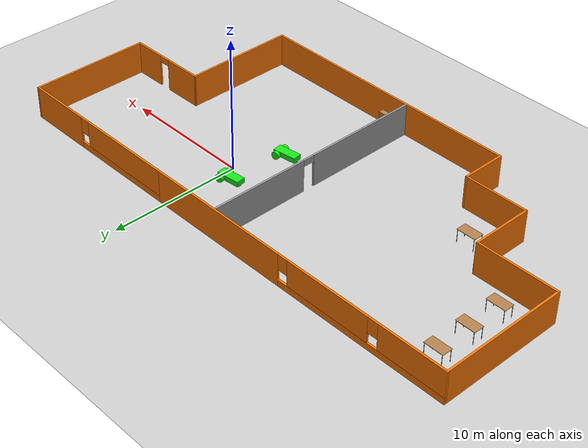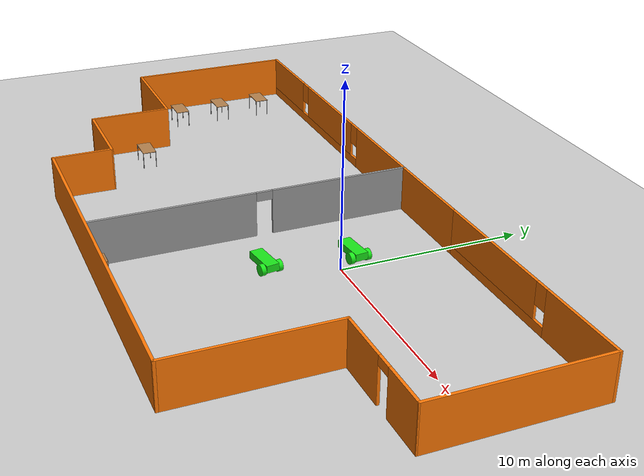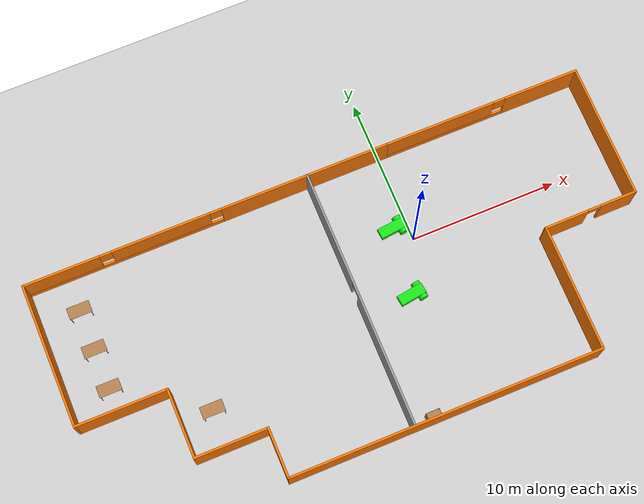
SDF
<sdf version="1.6">
 <world name="default">
  <plugin name="welcome" filename="libwelcome.so"/>
  <light name="sun" type="directional">
   <pose>0 0 10 0 -0 0</pose>
   <diffuse>0.8 0.8 0.8 1</diffuse>
   <specular>0.2 0.2 0.2 1</specular>
   <attenuation>
    <range>1000</range>
    <constant>0.9</constant>
    <linear>0.01</linear>
    <quadratic>0.001</quadratic>
   </attenuation>
   <direction>-0.5 0.1 -0.9</direction>
  </light>
  <model name="ground_plane">
   <static>1</static>
   <link name="link">
    <collision name="collision">
     <geometry><plane><normal>0 0 1</normal><size>100 100</size></plane></geometry>
     <surface><friction><ode><mu>100</mu><mu2>50</mu2></ode></friction></surface>
    </collision>
    <visual name="visual">
     <cast_shadows>0</cast_shadows>
     <geometry><plane><normal>0 0 1</normal><size>100 100</size></plane></geometry>
     <material>
      <script><uri>file://media/materials/scripts/gazebo.material</uri><name>Gazebo/Grey</name></script>
     </material>
    </visual>
   </link>
  </model>
  <gravity>0 0 -9.8</gravity>
  <magnetic_field>6e-06 2.3e-05 -4.2e-05</magnetic_field>
  <atmosphere type="adiabatic"/>
  <physics name="default_physics" default="0" type="ode">
   <max_step_size>0.001</max_step_size>
   <real_time_factor>1</real_time_factor>
   <real_time_update_rate>1000</real_time_update_rate>
  </physics>
  <scene><ambient>0.4 0.4 0.4 1</ambient><background>0.7 0.7 0.7 1</background><shadows>1</shadows></scene>
  <spherical_coordinates>
   <surface_model>EARTH_WGS84</surface_model>
   <latitude_deg>0</latitude_deg>
   <longitude_deg>0</longitude_deg>
   <elevation>0</elevation>
   <heading_deg>0</heading_deg>
  </spherical_coordinates>
  <model name="Vehicle_0">
   <link name="link_0_clone">
    <pose>0 -0 0.4 0 -0 0</pose>
    <inertial>
     <mass>8.4072</mass>
     <inertia><ixx>0.444437</ixx><ixy>0</ixy><ixz>0</ixz><iyy>1.39419</iyy><iyz>0</iyz><izz>1.60581</izz></inertia>
    </inertial>
    <visual name="visual">
     <geometry><box><size>1.8 0.7 0.4</size></box></geometry>
     <material>
      <lighting>1</lighting>
      <script><uri>file://media/materials/scripts/gazebo.material</uri><name>Gazebo/Grey</name></script>
      <shader type="pixel"><normal_map>__default__</normal_map></shader>
      <ambient>0.3 0.3 0.3 1</ambient>
      <diffuse>0.1 0.9 0.1 1</diffuse>
      <specular>0.01 0.01 0.01 1</specular>
      <emissive>0 0 0 1</emissive>
     </material>
    </visual>
    <collision name="collision">
     <geometry><box><size>1.8 0.7 0.4</size></box></geometry>
     <surface>
      <friction>
       <ode><mu>1</mu><mu2>1</mu2><fdir1>0 0 0</fdir1><slip1>0</slip1><slip2>0</slip2></ode>
       <torsional>
        <coefficient>1</coefficient>
        <patch_radius>0</patch_radius>
        <surface_radius>0</surface_radius>
        <use_patch_radius>1</use_patch_radius>
        <ode><slip>0</slip></ode>
       </torsional>
      </friction>
      <bounce><restitution_coefficient>0</restitution_coefficient><threshold>1e+06</threshold></bounce>
      <contact>
       <collide_without_contact>0</collide_without_contact>
       <collide_without_contact_bitmask>1</collide_without_contact_bitmask>
       <collide_bitmask>1</collide_bitmask>
       <ode>
        <soft_cfm>0</soft_cfm>
        <soft_erp>0.2</soft_erp>
        <kp>1e+13</kp>
        <kd>1</kd>
        <max_vel>0.01</max_vel>
        <min_depth>0</min_depth>
       </ode>
       <bullet>
        <split_impulse>1</split_impulse>
        <split_impulse_penetration_threshold>-0.01</split_impulse_penetration_threshold>
        <soft_cfm>0</soft_cfm>
        <soft_erp>0.2</soft_erp>
        <kp>1e+13</kp>
        <kd>1</kd>
       </bullet>
      </contact>
     </surface>
    </collision>
   </link>
   <link name="link_0">
    <pose>0.6 0.467205 0.3 1.5707 0.03 0</pose>
    <inertial>
     <mass>1</mass>
     <inertia><ixx>0.145833</ixx><ixy>0</ixy><ixz>0</ixz><iyy>0.145833</iyy><iyz>0</iyz><izz>0.125</izz></inertia>
    </inertial>
    <visual name="visual">
     <geometry><cylinder><radius>0.3</radius><length>0.25</length></cylinder></geometry>
     <material>
      <lighting>1</lighting>
      <script><uri>file://media/materials/scripts/gazebo.material</uri><name>Gazebo/Grey</name></script>
      <shader type="pixel"><normal_map>__default__</normal_map></shader>
      <ambient>0.3 0.3 0.3 1</ambient>
      <diffuse>0.1 0.9 0.1 1</diffuse>
      <specular>0.01 0.01 0.01 1</specular>
      <emissive>0 0 0 1</emissive>
     </material>
    </visual>
    <collision name="collision">
     <geometry><cylinder><radius>0.3</radius><length>0.25</length></cylinder></geometry>
     <surface>
      <friction>
       <ode><mu>1</mu><mu2>1</mu2><fdir1>0 0 0</fdir1><slip1>0</slip1><slip2>0</slip2></ode>
       <torsional>
        <coefficient>1</coefficient>
        <patch_radius>0</patch_radius>
        <surface_radius>0</surface_radius>
        <use_patch_radius>1</use_patch_radius>
        <ode><slip>0</slip></ode>
       </torsional>
      </friction>
      <bounce><restitution_coefficient>0</restitution_coefficient><threshold>1e+06</threshold></bounce>
      <contact>
       <collide_without_contact>0</collide_without_contact>
       <collide_without_contact_bitmask>1</collide_without_contact_bitmask>
       <collide_bitmask>1</collide_bitmask>
       <ode>
        <soft_cfm>0</soft_cfm>
        <soft_erp>0.2</soft_erp>
        <kp>1e+13</kp>
        <kd>1</kd>
        <max_vel>0.01</max_vel>
        <min_depth>0</min_depth>
       </ode>
       <bullet>
        <split_impulse>1</split_impulse>
        <split_impulse_penetration_threshold>-0.01</split_impulse_penetration_threshold>
        <soft_cfm>0</soft_cfm>
        <soft_erp>0.2</soft_erp>
        <kp>1e+13</kp>
        <kd>1</kd>
       </bullet>
      </contact>
     </surface>
    </collision>
   </link>
   <link name="link_0_0">
    <pose>-0.690774 0.00168 0.2 -0.031665 0.139995 0.005148</pose>
    <inertial>
     <mass>1</mass>
     <inertia><ixx>0.1</ixx><ixy>0</ixy><ixz>0</ixz><iyy>0.1</iyy><iyz>0</iyz><izz>0.1</izz></inertia>
    </inertial>
    <visual name="visual">
     <geometry><sphere><radius>0.2</radius></sphere></geometry>
     <material>
      <lighting>1</lighting>
      <script><uri>file://media/materials/scripts/gazebo.material</uri><name>Gazebo/Grey</name></script>
      <shader type="pixel"><normal_map>__default__</normal_map></shader>
      <ambient>0.3 0.3 0.3 1</ambient>
      <diffuse>0.7 0.7 0.7 1</diffuse>
      <specular>0.01 0.01 0.01 1</specular>
      <emissive>0 0 0 1</emissive>
     </material>
    </visual>
    <collision name="collision">
     <geometry><sphere><radius>0.2</radius></sphere></geometry>
     <surface>
      <friction>
       <ode><mu>1</mu><mu2>1</mu2><fdir1>0 0 0</fdir1><slip1>0</slip1><slip2>0</slip2></ode>
       <torsional>
        <coefficient>1</coefficient>
        <patch_radius>0</patch_radius>
        <surface_radius>0</surface_radius>
        <use_patch_radius>1</use_patch_radius>
        <ode><slip>0</slip></ode>
       </torsional>
      </friction>
      <bounce><restitution_coefficient>0</restitution_coefficient><threshold>1e+06</threshold></bounce>
      <contact>
       <collide_without_contact>0</collide_without_contact>
       <collide_without_contact_bitmask>1</collide_without_contact_bitmask>
       <collide_bitmask>1</collide_bitmask>
       <ode>
        <soft_cfm>0</soft_cfm>
        <soft_erp>0.2</soft_erp>
        <kp>1e+13</kp>
        <kd>1</kd>
        <max_vel>0.01</max_vel>
        <min_depth>0</min_depth>
       </ode>
       <bullet>
        <split_impulse>1</split_impulse>
        <split_impulse_penetration_threshold>-0.01</split_impulse_penetration_threshold>
        <soft_cfm>0</soft_cfm>
        <soft_erp>0.2</soft_erp>
        <kp>1e+13</kp>
        <kd>1</kd>
       </bullet>
      </contact>
     </surface>
    </collision>
   </link>
   <link name="link_0_clone_0">
    <pose>0.6 -0.475029 0.3 1.5707 -0 0</pose>
    <inertial>
     <mass>1</mass>
     <inertia><ixx>0.145833</ixx><ixy>0</ixy><ixz>0</ixz><iyy>0.145833</iyy><iyz>0</iyz><izz>0.125</izz></inertia>
    </inertial>
    <visual name="visual">
     <geometry><cylinder><radius>0.3</radius><length>0.25</length></cylinder></geometry>
     <material>
      <lighting>1</lighting>
      <script><uri>file://media/materials/scripts/gazebo.material</uri><name>Gazebo/Grey</name></script>
      <shader type="pixel"><normal_map>__default__</normal_map></shader>
      <ambient>0.3 0.3 0.3 1</ambient>
      <diffuse>0.1 0.9 0.1 1</diffuse>
      <specular>0.01 0.01 0.01 1</specular>
      <emissive>0 0 0 1</emissive>
     </material>
    </visual>
    <collision name="collision">
     <geometry><cylinder><radius>0.3</radius><length>0.25</length></cylinder></geometry>
     <surface>
      <friction>
       <ode><mu>1</mu><mu2>1</mu2><fdir1>0 0 0</fdir1><slip1>0</slip1><slip2>0</slip2></ode>
       <torsional>
        <coefficient>1</coefficient>
        <patch_radius>0</patch_radius>
        <surface_radius>0</surface_radius>
        <use_patch_radius>1</use_patch_radius>
        <ode><slip>0</slip></ode>
       </torsional>
      </friction>
      <bounce><restitution_coefficient>0</restitution_coefficient><threshold>1e+06</threshold></bounce>
      <contact>
       <collide_without_contact>0</collide_without_contact>
       <collide_without_contact_bitmask>1</collide_without_contact_bitmask>
       <collide_bitmask>1</collide_bitmask>
       <ode>
        <soft_cfm>0</soft_cfm>
        <soft_erp>0.2</soft_erp>
        <kp>1e+13</kp>
        <kd>1</kd>
        <max_vel>0.01</max_vel>
        <min_depth>0</min_depth>
       </ode>
       <bullet>
        <split_impulse>1</split_impulse>
        <split_impulse_penetration_threshold>-0.01</split_impulse_penetration_threshold>
        <soft_cfm>0</soft_cfm>
        <soft_erp>0.2</soft_erp>
        <kp>1e+13</kp>
        <kd>1</kd>
       </bullet>
      </contact>
     </surface>
    </collision>
   </link>
   <joint name="link_0_clone_JOINT_0_0" type="ball">
    <parent>link_0_clone</parent>
    <child>link_0_0</child>
    <physics>
     <ode><limit><cfm>0</cfm><erp>0.2</erp></limit><suspension><cfm>0</cfm><erp>0.2</erp></suspension></ode>
    </physics>
   </joint>
   <joint name="link_0_clone_JOINT_0" type="revolute">
    <parent>link_0_clone</parent>
    <child>link_0</child>
    <axis>
     <xyz>0 0 1</xyz>
     <use_parent_model_frame>0</use_parent_model_frame>
     <limit>
      <lower>-1.79769e+308</lower>
      <upper>1.79769e+308</upper>
      <effort>-1</effort>
      <velocity>-1</velocity>
     </limit>
     <dynamics>
      <spring_reference>0</spring_reference>
      <spring_stiffness>0</spring_stiffness>
      <damping>0</damping>
      <friction>0</friction>
     </dynamics>
    </axis>
    <physics>
     <ode><limit><cfm>0</cfm><erp>0.2</erp></limit><suspension><cfm>0</cfm><erp>0.2</erp></suspension></ode>
    </physics>
   </joint>
   <joint name="link_0_clone_JOINT_1" type="revolute">
    <parent>link_0_clone</parent>
    <child>link_0_clone_0</child>
    <axis>
     <xyz>0 0 1</xyz>
     <use_parent_model_frame>0</use_parent_model_frame>
     <limit>
      <lower>-1.79769e+308</lower>
      <upper>1.79769e+308</upper>
      <effort>-1</effort>
      <velocity>-1</velocity>
     </limit>
     <dynamics>
      <spring_reference>0</spring_reference>
      <spring_stiffness>0</spring_stiffness>
      <damping>0</damping>
      <friction>0</friction>
     </dynamics>
    </axis>
    <physics>
     <ode><limit><cfm>0</cfm><erp>0.2</erp></limit><suspension><cfm>0</cfm><erp>0.2</erp></suspension></ode>
    </physics>
   </joint>
   <static>0</static>
   <pose>-1.6259 -3.46244 6e-06 0 -9e-06 0.142603</pose>
  </model>
  <model name="Vehicle">
   <link name="link_0_clone">
    <pose>0 -0 0.4 0 -0 0</pose>
    <inertial>
     <mass>8.4072</mass>
     <inertia><ixx>0.444437</ixx><ixy>0</ixy><ixz>0</ixz><iyy>1.39419</iyy><iyz>0</iyz><izz>1.60581</izz></inertia>
    </inertial>
    <visual name="visual">
     <geometry><box><size>1.8 0.7 0.4</size></box></geometry>
     <material>
      <lighting>1</lighting>
      <script><uri>file://media/materials/scripts/gazebo.material</uri><name>Gazebo/Grey</name></script>
      <shader type="pixel"><normal_map>__default__</normal_map></shader>
      <ambient>0.3 0.3 0.3 1</ambient>
      <diffuse>0.1 0.9 0.1 1</diffuse>
      <specular>0.01 0.01 0.01 1</specular>
      <emissive>0 0 0 1</emissive>
     </material>
    </visual>
    <collision name="collision">
     <geometry><box><size>1.8 0.7 0.4</size></box></geometry>
     <surface>
      <friction>
       <ode><mu>1</mu><mu2>1</mu2><fdir1>0 0 0</fdir1><slip1>0</slip1><slip2>0</slip2></ode>
       <torsional>
        <coefficient>1</coefficient>
        <patch_radius>0</patch_radius>
        <surface_radius>0</surface_radius>
        <use_patch_radius>1</use_patch_radius>
        <ode><slip>0</slip></ode>
       </torsional>
      </friction>
      <bounce><restitution_coefficient>0</restitution_coefficient><threshold>1e+06</threshold></bounce>
      <contact>
       <collide_without_contact>0</collide_without_contact>
       <collide_without_contact_bitmask>1</collide_without_contact_bitmask>
       <collide_bitmask>1</collide_bitmask>
       <ode>
        <soft_cfm>0</soft_cfm>
        <soft_erp>0.2</soft_erp>
        <kp>1e+13</kp>
        <kd>1</kd>
        <max_vel>0.01</max_vel>
        <min_depth>0</min_depth>
       </ode>
       <bullet>
        <split_impulse>1</split_impulse>
        <split_impulse_penetration_threshold>-0.01</split_impulse_penetration_threshold>
        <soft_cfm>0</soft_cfm>
        <soft_erp>0.2</soft_erp>
        <kp>1e+13</kp>
        <kd>1</kd>
       </bullet>
      </contact>
     </surface>
    </collision>
   </link>
   <link name="link_0">
    <pose>0.6 0.467205 0.3 1.5707 0.03 0</pose>
    <inertial>
     <mass>1</mass>
     <inertia><ixx>0.145833</ixx><ixy>0</ixy><ixz>0</ixz><iyy>0.145833</iyy><iyz>0</iyz><izz>0.125</izz></inertia>
    </inertial>
    <visual name="visual">
     <geometry><cylinder><radius>0.3</radius><length>0.25</length></cylinder></geometry>
     <material>
      <lighting>1</lighting>
      <script><uri>file://media/materials/scripts/gazebo.material</uri><name>Gazebo/Grey</name></script>
      <shader type="pixel"><normal_map>__default__</normal_map></shader>
      <ambient>0.3 0.3 0.3 1</ambient>
      <diffuse>0.1 0.9 0.1 1</diffuse>
      <specular>0.01 0.01 0.01 1</specular>
      <emissive>0 0 0 1</emissive>
     </material>
    </visual>
    <collision name="collision">
     <geometry><cylinder><radius>0.3</radius><length>0.25</length></cylinder></geometry>
     <surface>
      <friction>
       <ode><mu>1</mu><mu2>1</mu2><fdir1>0 0 0</fdir1><slip1>0</slip1><slip2>0</slip2></ode>
       <torsional>
        <coefficient>1</coefficient>
        <patch_radius>0</patch_radius>
        <surface_radius>0</surface_radius>
        <use_patch_radius>1</use_patch_radius>
        <ode><slip>0</slip></ode>
       </torsional>
      </friction>
      <bounce><restitution_coefficient>0</restitution_coefficient><threshold>1e+06</threshold></bounce>
      <contact>
       <collide_without_contact>0</collide_without_contact>
       <collide_without_contact_bitmask>1</collide_without_contact_bitmask>
       <collide_bitmask>1</collide_bitmask>
       <ode>
        <soft_cfm>0</soft_cfm>
        <soft_erp>0.2</soft_erp>
        <kp>1e+13</kp>
        <kd>1</kd>
        <max_vel>0.01</max_vel>
        <min_depth>0</min_depth>
       </ode>
       <bullet>
        <split_impulse>1</split_impulse>
        <split_impulse_penetration_threshold>-0.01</split_impulse_penetration_threshold>
        <soft_cfm>0</soft_cfm>
        <soft_erp>0.2</soft_erp>
        <kp>1e+13</kp>
        <kd>1</kd>
       </bullet>
      </contact>
     </surface>
    </collision>
   </link>
   <link name="link_0_0">
    <pose>-0.690774 0.00168 0.2 -0.031665 0.139995 0.005148</pose>
    <inertial>
     <mass>1</mass>
     <inertia><ixx>0.1</ixx><ixy>0</ixy><ixz>0</ixz><iyy>0.1</iyy><iyz>0</iyz><izz>0.1</izz></inertia>
    </inertial>
    <visual name="visual">
     <geometry><sphere><radius>0.2</radius></sphere></geometry>
     <material>
      <lighting>1</lighting>
      <script><uri>file://media/materials/scripts/gazebo.material</uri><name>Gazebo/Grey</name></script>
      <shader type="pixel"><normal_map>__default__</normal_map></shader>
      <ambient>0.3 0.3 0.3 1</ambient>
      <diffuse>0.7 0.7 0.7 1</diffuse>
      <specular>0.01 0.01 0.01 1</specular>
      <emissive>0 0 0 1</emissive>
     </material>
    </visual>
    <collision name="collision">
     <geometry><sphere><radius>0.2</radius></sphere></geometry>
     <surface>
      <friction>
       <ode><mu>1</mu><mu2>1</mu2><fdir1>0 0 0</fdir1><slip1>0</slip1><slip2>0</slip2></ode>
       <torsional>
        <coefficient>1</coefficient>
        <patch_radius>0</patch_radius>
        <surface_radius>0</surface_radius>
        <use_patch_radius>1</use_patch_radius>
        <ode><slip>0</slip></ode>
       </torsional>
      </friction>
      <bounce><restitution_coefficient>0</restitution_coefficient><threshold>1e+06</threshold></bounce>
      <contact>
       <collide_without_contact>0</collide_without_contact>
       <collide_without_contact_bitmask>1</collide_without_contact_bitmask>
       <collide_bitmask>1</collide_bitmask>
       <ode>
        <soft_cfm>0</soft_cfm>
        <soft_erp>0.2</soft_erp>
        <kp>1e+13</kp>
        <kd>1</kd>
        <max_vel>0.01</max_vel>
        <min_depth>0</min_depth>
       </ode>
       <bullet>
        <split_impulse>1</split_impulse>
        <split_impulse_penetration_threshold>-0.01</split_impulse_penetration_threshold>
        <soft_cfm>0</soft_cfm>
        <soft_erp>0.2</soft_erp>
        <kp>1e+13</kp>
        <kd>1</kd>
       </bullet>
      </contact>
     </surface>
    </collision>
   </link>
   <link name="link_0_clone_0">
    <pose>0.6 -0.475029 0.3 1.5707 -0 0</pose>
    <inertial>
     <mass>1</mass>
     <inertia><ixx>0.145833</ixx><ixy>0</ixy><ixz>0</ixz><iyy>0.145833</iyy><iyz>0</iyz><izz>0.125</izz></inertia>
    </inertial>
    <visual name="visual">
     <geometry><cylinder><radius>0.3</radius><length>0.25</length></cylinder></geometry>
     <material>
      <lighting>1</lighting>
      <script><uri>file://media/materials/scripts/gazebo.material</uri><name>Gazebo/Grey</name></script>
      <shader type="pixel"><normal_map>__default__</normal_map></shader>
      <ambient>0.3 0.3 0.3 1</ambient>
      <diffuse>0.1 0.9 0.1 1</diffuse>
      <specular>0.01 0.01 0.01 1</specular>
      <emissive>0 0 0 1</emissive>
     </material>
    </visual>
    <collision name="collision">
     <geometry><cylinder><radius>0.3</radius><length>0.25</length></cylinder></geometry>
     <surface>
      <friction>
       <ode><mu>1</mu><mu2>1</mu2><fdir1>0 0 0</fdir1><slip1>0</slip1><slip2>0</slip2></ode>
       <torsional>
        <coefficient>1</coefficient>
        <patch_radius>0</patch_radius>
        <surface_radius>0</surface_radius>
        <use_patch_radius>1</use_patch_radius>
        <ode><slip>0</slip></ode>
       </torsional>
      </friction>
      <bounce><restitution_coefficient>0</restitution_coefficient><threshold>1e+06</threshold></bounce>
      <contact>
       <collide_without_contact>0</collide_without_contact>
       <collide_without_contact_bitmask>1</collide_without_contact_bitmask>
       <collide_bitmask>1</collide_bitmask>
       <ode>
        <soft_cfm>0</soft_cfm>
        <soft_erp>0.2</soft_erp>
        <kp>1e+13</kp>
        <kd>1</kd>
        <max_vel>0.01</max_vel>
        <min_depth>0</min_depth>
       </ode>
       <bullet>
        <split_impulse>1</split_impulse>
        <split_impulse_penetration_threshold>-0.01</split_impulse_penetration_threshold>
        <soft_cfm>0</soft_cfm>
        <soft_erp>0.2</soft_erp>
        <kp>1e+13</kp>
        <kd>1</kd>
       </bullet>
      </contact>
     </surface>
    </collision>
   </link>
   <joint name="link_0_clone_JOINT_0_0" type="ball">
    <parent>link_0_clone</parent>
    <child>link_0_0</child>
    <physics>
     <ode><limit><cfm>0</cfm><erp>0.2</erp></limit><suspension><cfm>0</cfm><erp>0.2</erp></suspension></ode>
    </physics>
   </joint>
   <joint name="link_0_clone_JOINT_0" type="revolute">
    <parent>link_0_clone</parent>
    <child>link_0</child>
    <axis>
     <xyz>0 0 1</xyz>
     <use_parent_model_frame>0</use_parent_model_frame>
     <limit>
      <lower>-1.79769e+308</lower>
      <upper>1.79769e+308</upper>
      <effort>-1</effort>
      <velocity>-1</velocity>
     </limit>
     <dynamics>
      <spring_reference>0</spring_reference>
      <spring_stiffness>0</spring_stiffness>
      <damping>0</damping>
      <friction>0</friction>
     </dynamics>
    </axis>
    <physics>
     <ode><limit><cfm>0</cfm><erp>0.2</erp></limit><suspension><cfm>0</cfm><erp>0.2</erp></suspension></ode>
    </physics>
   </joint>
   <joint name="link_0_clone_JOINT_1" type="revolute">
    <parent>link_0_clone</parent>
    <child>link_0_clone_0</child>
    <axis>
     <xyz>0 0 1</xyz>
     <use_parent_model_frame>0</use_parent_model_frame>
     <limit>
      <lower>-1.79769e+308</lower>
      <upper>1.79769e+308</upper>
      <effort>-1</effort>
      <velocity>-1</velocity>
     </limit>
     <dynamics>
      <spring_reference>0</spring_reference>
      <spring_stiffness>0</spring_stiffness>
      <damping>0</damping>
      <friction>0</friction>
     </dynamics>
    </axis>
    <physics>
     <ode><limit><cfm>0</cfm><erp>0.2</erp></limit><suspension><cfm>0</cfm><erp>0.2</erp></suspension></ode>
    </physics>
   </joint>
   <static>0</static>
   <pose>-1.04094 1.11648 3e-06 1e-06 -1.5e-05 0.107594</pose>
  </model>
  <model name="Building">
   <link name="Wall_0">
    <pose>-6.7329 8.76145 0 0 -0 3.14159</pose>
    <visual name="Wall_0_Visual_5">
     <pose>6.91914 0 1.9 0 -0 0</pose>
     <geometry><box><size>0.8 0.15 1.2</size></box></geometry>
     <material>
      <script><uri>file://media/materials/scripts/gazebo.material</uri><name>Gazebo/Grey</name></script>
      <ambient>0.996078 0.47451 0.0196078 1</ambient>
      <shader type="pixel"/>
      <diffuse>0.7 0.7 0.7 1</diffuse>
      <specular>0.01 0.01 0.01 1</specular>
      <emissive>0 0 0 1</emissive>
     </material>
     <meta><layer>0</layer></meta>
    </visual>
    <visual name="Wall_0_Visual_0">
     <pose>-6.73561 0 1.25 0 -0 0</pose>
     <geometry><box><size>11.5288 0.15 2.5</size></box></geometry>
     <material>
      <script><uri>file://media/materials/scripts/gazebo.material</uri><name>Gazebo/Grey</name></script>
      <ambient>0.996078 0.47451 0.0196078 1</ambient>
      <shader type="pixel"/>
      <diffuse>0.7 0.7 0.7 1</diffuse>
      <specular>0.01 0.01 0.01 1</specular>
      <emissive>0 0 0 1</emissive>
     </material>
     <meta><layer>0</layer></meta>
    </visual>
    <visual name="Wall_0_Visual_2">
     <pose>3.17396 0 1.5 0 -0 0</pose>
     <geometry><box><size>6.69035 0.15 2</size></box></geometry>
     <material>
      <script><uri>file://media/materials/scripts/gazebo.material</uri><name>Gazebo/Grey</name></script>
      <ambient>0.996078 0.47451 0.0196078 1</ambient>
      <shader type="pixel"/>
      <diffuse>0.7 0.7 0.7 1</diffuse>
      <specular>0.01 0.01 0.01 1</specular>
      <emissive>0 0 0 1</emissive>
     </material>
     <meta><layer>0</layer></meta>
    </visual>
    <visual name="Wall_0_Visual_1">
     <pose>5.76439 0 0.25 0 -0 0</pose>
     <geometry><box><size>13.4712 0.15 0.5</size></box></geometry>
     <material>
      <script><uri>file://media/materials/scripts/gazebo.material</uri><name>Gazebo/Grey</name></script>
      <ambient>0.996078 0.47451 0.0196078 1</ambient>
      <shader type="pixel"/>
      <diffuse>0.7 0.7 0.7 1</diffuse>
      <specular>0.01 0.01 0.01 1</specular>
      <emissive>0 0 0 1</emissive>
     </material>
     <meta><layer>0</layer></meta>
    </visual>
    <visual name="Wall_0_Visual_3">
     <pose>9.90957 0 1.5 0 -0 0</pose>
     <geometry><box><size>5.18086 0.15 2</size></box></geometry>
     <material>
      <script><uri>file://media/materials/scripts/gazebo.material</uri><name>Gazebo/Grey</name></script>
      <ambient>0.996078 0.47451 0.0196078 1</ambient>
      <shader type="pixel"/>
      <diffuse>0.7 0.7 0.7 1</diffuse>
      <specular>0.01 0.01 0.01 1</specular>
      <emissive>0 0 0 1</emissive>
     </material>
     <meta><layer>0</layer></meta>
    </visual>
    <visual name="Wall_0_Visual_4">
     <pose>-0.571214 0 1.9 0 -0 0</pose>
     <geometry><box><size>0.8 0.15 1.2</size></box></geometry>
     <material>
      <script><uri>file://media/materials/scripts/gazebo.material</uri><name>Gazebo/Grey</name></script>
      <ambient>0.996078 0.47451 0.0196078 1</ambient>
      <shader type="pixel"/>
      <diffuse>0.7 0.7 0.7 1</diffuse>
      <specular>0.01 0.01 0.01 1</specular>
      <emissive>0 0 0 1</emissive>
     </material>
     <meta><layer>0</layer></meta>
    </visual>
    <collision name="Wall_0_Collision_5">
     <pose>6.91914 0 1.9 0 -0 0</pose>
     <geometry><box><size>0.8 0.15 1.2</size></box></geometry>
     <surface>
      <friction>
       <ode><mu>1</mu><mu2>1</mu2><fdir1>0 0 0</fdir1><slip1>0</slip1><slip2>0</slip2></ode>
       <torsional>
        <coefficient>1</coefficient>
        <patch_radius>0</patch_radius>
        <surface_radius>0</surface_radius>
        <use_patch_radius>1</use_patch_radius>
        <ode><slip>0</slip></ode>
       </torsional>
      </friction>
      <bounce><restitution_coefficient>0</restitution_coefficient><threshold>1e+06</threshold></bounce>
      <contact>
       <collide_without_contact>0</collide_without_contact>
       <collide_without_contact_bitmask>1</collide_without_contact_bitmask>
       <collide_bitmask>1</collide_bitmask>
       <ode>
        <soft_cfm>0</soft_cfm>
        <soft_erp>0.2</soft_erp>
        <kp>1e+13</kp>
        <kd>1</kd>
        <max_vel>0.01</max_vel>
        <min_depth>0</min_depth>
       </ode>
       <bullet>
        <split_impulse>1</split_impulse>
        <split_impulse_penetration_threshold>-0.01</split_impulse_penetration_threshold>
        <soft_cfm>0</soft_cfm>
        <soft_erp>0.2</soft_erp>
        <kp>1e+13</kp>
        <kd>1</kd>
       </bullet>
      </contact>
     </surface>
    </collision>
    <collision name="Wall_0_Collision_3">
     <pose>9.90957 0 1.5 0 -0 0</pose>
     <geometry><box><size>5.18086 0.15 2</size></box></geometry>
     <surface>
      <friction>
       <ode><mu>1</mu><mu2>1</mu2><fdir1>0 0 0</fdir1><slip1>0</slip1><slip2>0</slip2></ode>
       <torsional>
        <coefficient>1</coefficient>
        <patch_radius>0</patch_radius>
        <surface_radius>0</surface_radius>
        <use_patch_radius>1</use_patch_radius>
        <ode><slip>0</slip></ode>
       </torsional>
      </friction>
      <bounce><restitution_coefficient>0</restitution_coefficient><threshold>1e+06</threshold></bounce>
      <contact>
       <collide_without_contact>0</collide_without_contact>
       <collide_without_contact_bitmask>1</collide_without_contact_bitmask>
       <collide_bitmask>1</collide_bitmask>
       <ode>
        <soft_cfm>0</soft_cfm>
        <soft_erp>0.2</soft_erp>
        <kp>1e+13</kp>
        <kd>1</kd>
        <max_vel>0.01</max_vel>
        <min_depth>0</min_depth>
       </ode>
       <bullet>
        <split_impulse>1</split_impulse>
        <split_impulse_penetration_threshold>-0.01</split_impulse_penetration_threshold>
        <soft_cfm>0</soft_cfm>
        <soft_erp>0.2</soft_erp>
        <kp>1e+13</kp>
        <kd>1</kd>
       </bullet>
      </contact>
     </surface>
    </collision>
    <collision name="Wall_0_Collision_2">
     <pose>3.17396 0 1.5 0 -0 0</pose>
     <geometry><box><size>6.69035 0.15 2</size></box></geometry>
     <surface>
      <friction>
       <ode><mu>1</mu><mu2>1</mu2><fdir1>0 0 0</fdir1><slip1>0</slip1><slip2>0</slip2></ode>
       <torsional>
        <coefficient>1</coefficient>
        <patch_radius>0</patch_radius>
        <surface_radius>0</surface_radius>
        <use_patch_radius>1</use_patch_radius>
        <ode><slip>0</slip></ode>
       </torsional>
      </friction>
      <bounce><restitution_coefficient>0</restitution_coefficient><threshold>1e+06</threshold></bounce>
      <contact>
       <collide_without_contact>0</collide_without_contact>
       <collide_without_contact_bitmask>1</collide_without_contact_bitmask>
       <collide_bitmask>1</collide_bitmask>
       <ode>
        <soft_cfm>0</soft_cfm>
        <soft_erp>0.2</soft_erp>
        <kp>1e+13</kp>
        <kd>1</kd>
        <max_vel>0.01</max_vel>
        <min_depth>0</min_depth>
       </ode>
       <bullet>
        <split_impulse>1</split_impulse>
        <split_impulse_penetration_threshold>-0.01</split_impulse_penetration_threshold>
        <soft_cfm>0</soft_cfm>
        <soft_erp>0.2</soft_erp>
        <kp>1e+13</kp>
        <kd>1</kd>
       </bullet>
      </contact>
     </surface>
    </collision>
    <collision name="Wall_0_Collision_4">
     <pose>-0.571214 0 1.9 0 -0 0</pose>
     <geometry><box><size>0.8 0.15 1.2</size></box></geometry>
     <surface>
      <friction>
       <ode><mu>1</mu><mu2>1</mu2><fdir1>0 0 0</fdir1><slip1>0</slip1><slip2>0</slip2></ode>
       <torsional>
        <coefficient>1</coefficient>
        <patch_radius>0</patch_radius>
        <surface_radius>0</surface_radius>
        <use_patch_radius>1</use_patch_radius>
        <ode><slip>0</slip></ode>
       </torsional>
      </friction>
      <bounce><restitution_coefficient>0</restitution_coefficient><threshold>1e+06</threshold></bounce>
      <contact>
       <collide_without_contact>0</collide_without_contact>
       <collide_without_contact_bitmask>1</collide_without_contact_bitmask>
       <collide_bitmask>1</collide_bitmask>
       <ode>
        <soft_cfm>0</soft_cfm>
        <soft_erp>0.2</soft_erp>
        <kp>1e+13</kp>
        <kd>1</kd>
        <max_vel>0.01</max_vel>
        <min_depth>0</min_depth>
       </ode>
       <bullet>
        <split_impulse>1</split_impulse>
        <split_impulse_penetration_threshold>-0.01</split_impulse_penetration_threshold>
        <soft_cfm>0</soft_cfm>
        <soft_erp>0.2</soft_erp>
        <kp>1e+13</kp>
        <kd>1</kd>
       </bullet>
      </contact>
     </surface>
    </collision>
    <collision name="Wall_0_Collision_0">
     <pose>-6.73561 0 1.25 0 -0 0</pose>
     <geometry><box><size>11.5288 0.15 2.5</size></box></geometry>
     <surface>
      <friction>
       <ode><mu>1</mu><mu2>1</mu2><fdir1>0 0 0</fdir1><slip1>0</slip1><slip2>0</slip2></ode>
       <torsional>
        <coefficient>1</coefficient>
        <patch_radius>0</patch_radius>
        <surface_radius>0</surface_radius>
        <use_patch_radius>1</use_patch_radius>
        <ode><slip>0</slip></ode>
       </torsional>
      </friction>
      <bounce><restitution_coefficient>0</restitution_coefficient><threshold>1e+06</threshold></bounce>
      <contact>
       <collide_without_contact>0</collide_without_contact>
       <collide_without_contact_bitmask>1</collide_without_contact_bitmask>
       <collide_bitmask>1</collide_bitmask>
       <ode>
        <soft_cfm>0</soft_cfm>
        <soft_erp>0.2</soft_erp>
        <kp>1e+13</kp>
        <kd>1</kd>
        <max_vel>0.01</max_vel>
        <min_depth>0</min_depth>
       </ode>
       <bullet>
        <split_impulse>1</split_impulse>
        <split_impulse_penetration_threshold>-0.01</split_impulse_penetration_threshold>
        <soft_cfm>0</soft_cfm>
        <soft_erp>0.2</soft_erp>
        <kp>1e+13</kp>
        <kd>1</kd>
       </bullet>
      </contact>
     </surface>
    </collision>
    <collision name="Wall_0_Collision_1">
     <pose>5.76439 0 0.25 0 -0 0</pose>
     <geometry><box><size>13.4712 0.15 0.5</size></box></geometry>
     <surface>
      <friction>
       <ode><mu>1</mu><mu2>1</mu2><fdir1>0 0 0</fdir1><slip1>0</slip1><slip2>0</slip2></ode>
       <torsional>
        <coefficient>1</coefficient>
        <patch_radius>0</patch_radius>
        <surface_radius>0</surface_radius>
        <use_patch_radius>1</use_patch_radius>
        <ode><slip>0</slip></ode>
       </torsional>
      </friction>
      <bounce><restitution_coefficient>0</restitution_coefficient><threshold>1e+06</threshold></bounce>
      <contact>
       <collide_without_contact>0</collide_without_contact>
       <collide_without_contact_bitmask>1</collide_without_contact_bitmask>
       <collide_bitmask>1</collide_bitmask>
       <ode>
        <soft_cfm>0</soft_cfm>
        <soft_erp>0.2</soft_erp>
        <kp>1e+13</kp>
        <kd>1</kd>
        <max_vel>0.01</max_vel>
        <min_depth>0</min_depth>
       </ode>
       <bullet>
        <split_impulse>1</split_impulse>
        <split_impulse_penetration_threshold>-0.01</split_impulse_penetration_threshold>
        <soft_cfm>0</soft_cfm>
        <soft_erp>0.2</soft_erp>
        <kp>1e+13</kp>
        <kd>1</kd>
       </bullet>
      </contact>
     </surface>
    </collision>
   </link>
   <link name="Wall_1">
    <pose>-19.1579 3.96145 0 0 0 -1.5708</pose>
    <visual name="Wall_1_Visual">
     <pose>0 0 1.25 0 -0 0</pose>
     <geometry><box><size>9.75 0.15 2.5</size></box></geometry>
     <material>
      <script><uri>file://media/materials/scripts/gazebo.material</uri><name>Gazebo/Grey</name></script>
      <ambient>0.996078 0.47451 0.0196078 1</ambient>
      <shader type="pixel"/>
      <diffuse>0.7 0.7 0.7 1</diffuse>
      <specular>0.01 0.01 0.01 1</specular>
      <emissive>0 0 0 1</emissive>
     </material>
     <meta><layer>0</layer></meta>
    </visual>
    <collision name="Wall_1_Collision">
     <pose>0 0 1.25 0 -0 0</pose>
     <geometry><box><size>9.75 0.15 2.5</size></box></geometry>
     <surface>
      <friction>
       <ode><mu>1</mu><mu2>1</mu2><fdir1>0 0 0</fdir1><slip1>0</slip1><slip2>0</slip2></ode>
       <torsional>
        <coefficient>1</coefficient>
        <patch_radius>0</patch_radius>
        <surface_radius>0</surface_radius>
        <use_patch_radius>1</use_patch_radius>
        <ode><slip>0</slip></ode>
       </torsional>
      </friction>
      <bounce><restitution_coefficient>0</restitution_coefficient><threshold>1e+06</threshold></bounce>
      <contact>
       <collide_without_contact>0</collide_without_contact>
       <collide_without_contact_bitmask>1</collide_without_contact_bitmask>
       <collide_bitmask>1</collide_bitmask>
       <ode>
        <soft_cfm>0</soft_cfm>
        <soft_erp>0.2</soft_erp>
        <kp>1e+13</kp>
        <kd>1</kd>
        <max_vel>0.01</max_vel>
        <min_depth>0</min_depth>
       </ode>
       <bullet>
        <split_impulse>1</split_impulse>
        <split_impulse_penetration_threshold>-0.01</split_impulse_penetration_threshold>
        <soft_cfm>0</soft_cfm>
        <soft_erp>0.2</soft_erp>
        <kp>1e+13</kp>
        <kd>1</kd>
       </bullet>
      </contact>
     </surface>
    </collision>
   </link>
   <link name="Wall_10">
    <pose>12.4248 8.76151 0 0 0 -3.14159</pose>
    <visual name="Wall_10_Visual_1">
     <pose>2.58746 0 0.25 0 -0 0</pose>
     <geometry><box><size>8.4404 0.15 0.5</size></box></geometry>
     <material>
      <script><uri>file://media/materials/scripts/gazebo.material</uri><name>Gazebo/Grey</name></script>
      <ambient>0.996078 0.47451 0.0196078 1</ambient>
      <shader type="pixel"/>
      <diffuse>0.7 0.7 0.7 1</diffuse>
      <specular>0.01 0.01 0.01 1</specular>
      <emissive>0 0 0 1</emissive>
     </material>
     <meta><layer>0</layer></meta>
    </visual>
    <visual name="Wall_10_Visual_2">
     <pose>2.98746 0 1.5 0 -0 0</pose>
     <geometry><box><size>7.6404 0.15 2</size></box></geometry>
     <material>
      <script><uri>file://media/materials/scripts/gazebo.material</uri><name>Gazebo/Grey</name></script>
      <ambient>0.996078 0.47451 0.0196078 1</ambient>
      <shader type="pixel"/>
      <diffuse>0.7 0.7 0.7 1</diffuse>
      <specular>0.01 0.01 0.01 1</specular>
      <emissive>0 0 0 1</emissive>
     </material>
     <meta><layer>0</layer></meta>
    </visual>
    <visual name="Wall_10_Visual_0">
     <pose>-4.2202 0 1.25 0 -0 0</pose>
     <geometry><box><size>5.17492 0.15 2.5</size></box></geometry>
     <material>
      <script><uri>file://media/materials/scripts/gazebo.material</uri><name>Gazebo/Grey</name></script>
      <ambient>0.996078 0.47451 0.0196078 1</ambient>
      <shader type="pixel"/>
      <diffuse>0.7 0.7 0.7 1</diffuse>
      <specular>0.01 0.01 0.01 1</specular>
      <emissive>0 0 0 1</emissive>
     </material>
     <meta><layer>0</layer></meta>
    </visual>
    <visual name="Wall_10_Visual_3">
     <pose>-1.23274 0 1.9 0 -0 0</pose>
     <geometry><box><size>0.8 0.15 1.2</size></box></geometry>
     <material>
      <script><uri>file://media/materials/scripts/gazebo.material</uri><name>Gazebo/Grey</name></script>
      <ambient>0.996078 0.47451 0.0196078 1</ambient>
      <shader type="pixel"/>
      <diffuse>0.7 0.7 0.7 1</diffuse>
      <specular>0.01 0.01 0.01 1</specular>
      <emissive>0 0 0 1</emissive>
     </material>
     <meta><layer>0</layer></meta>
    </visual>
    <collision name="Wall_10_Collision_3">
     <pose>-1.23274 0 1.9 0 -0 0</pose>
     <geometry><box><size>0.8 0.15 1.2</size></box></geometry>
     <surface>
      <friction>
       <ode><mu>1</mu><mu2>1</mu2><fdir1>0 0 0</fdir1><slip1>0</slip1><slip2>0</slip2></ode>
       <torsional>
        <coefficient>1</coefficient>
        <patch_radius>0</patch_radius>
        <surface_radius>0</surface_radius>
        <use_patch_radius>1</use_patch_radius>
        <ode><slip>0</slip></ode>
       </torsional>
      </friction>
      <bounce><restitution_coefficient>0</restitution_coefficient><threshold>1e+06</threshold></bounce>
      <contact>
       <collide_without_contact>0</collide_without_contact>
       <collide_without_contact_bitmask>1</collide_without_contact_bitmask>
       <collide_bitmask>1</collide_bitmask>
       <ode>
        <soft_cfm>0</soft_cfm>
        <soft_erp>0.2</soft_erp>
        <kp>1e+13</kp>
        <kd>1</kd>
        <max_vel>0.01</max_vel>
        <min_depth>0</min_depth>
       </ode>
       <bullet>
        <split_impulse>1</split_impulse>
        <split_impulse_penetration_threshold>-0.01</split_impulse_penetration_threshold>
        <soft_cfm>0</soft_cfm>
        <soft_erp>0.2</soft_erp>
        <kp>1e+13</kp>
        <kd>1</kd>
       </bullet>
      </contact>
     </surface>
    </collision>
    <collision name="Wall_10_Collision_1">
     <pose>2.58746 0 0.25 0 -0 0</pose>
     <geometry><box><size>8.4404 0.15 0.5</size></box></geometry>
     <surface>
      <friction>
       <ode><mu>1</mu><mu2>1</mu2><fdir1>0 0 0</fdir1><slip1>0</slip1><slip2>0</slip2></ode>
       <torsional>
        <coefficient>1</coefficient>
        <patch_radius>0</patch_radius>
        <surface_radius>0</surface_radius>
        <use_patch_radius>1</use_patch_radius>
        <ode><slip>0</slip></ode>
       </torsional>
      </friction>
      <bounce><restitution_coefficient>0</restitution_coefficient><threshold>1e+06</threshold></bounce>
      <contact>
       <collide_without_contact>0</collide_without_contact>
       <collide_without_contact_bitmask>1</collide_without_contact_bitmask>
       <collide_bitmask>1</collide_bitmask>
       <ode>
        <soft_cfm>0</soft_cfm>
        <soft_erp>0.2</soft_erp>
        <kp>1e+13</kp>
        <kd>1</kd>
        <max_vel>0.01</max_vel>
        <min_depth>0</min_depth>
       </ode>
       <bullet>
        <split_impulse>1</split_impulse>
        <split_impulse_penetration_threshold>-0.01</split_impulse_penetration_threshold>
        <soft_cfm>0</soft_cfm>
        <soft_erp>0.2</soft_erp>
        <kp>1e+13</kp>
        <kd>1</kd>
       </bullet>
      </contact>
     </surface>
    </collision>
    <collision name="Wall_10_Collision_2">
     <pose>2.98746 0 1.5 0 -0 0</pose>
     <geometry><box><size>7.6404 0.15 2</size></box></geometry>
     <surface>
      <friction>
       <ode><mu>1</mu><mu2>1</mu2><fdir1>0 0 0</fdir1><slip1>0</slip1><slip2>0</slip2></ode>
       <torsional>
        <coefficient>1</coefficient>
        <patch_radius>0</patch_radius>
        <surface_radius>0</surface_radius>
        <use_patch_radius>1</use_patch_radius>
        <ode><slip>0</slip></ode>
       </torsional>
      </friction>
      <bounce><restitution_coefficient>0</restitution_coefficient><threshold>1e+06</threshold></bounce>
      <contact>
       <collide_without_contact>0</collide_without_contact>
       <collide_without_contact_bitmask>1</collide_without_contact_bitmask>
       <collide_bitmask>1</collide_bitmask>
       <ode>
        <soft_cfm>0</soft_cfm>
        <soft_erp>0.2</soft_erp>
        <kp>1e+13</kp>
        <kd>1</kd>
        <max_vel>0.01</max_vel>
        <min_depth>0</min_depth>
       </ode>
       <bullet>
        <split_impulse>1</split_impulse>
        <split_impulse_penetration_threshold>-0.01</split_impulse_penetration_threshold>
        <soft_cfm>0</soft_cfm>
        <soft_erp>0.2</soft_erp>
        <kp>1e+13</kp>
        <kd>1</kd>
       </bullet>
      </contact>
     </surface>
    </collision>
    <collision name="Wall_10_Collision_0">
     <pose>-4.2202 0 1.25 0 -0 0</pose>
     <geometry><box><size>5.17492 0.15 2.5</size></box></geometry>
     <surface>
      <friction>
       <ode><mu>1</mu><mu2>1</mu2><fdir1>0 0 0</fdir1><slip1>0</slip1><slip2>0</slip2></ode>
       <torsional>
        <coefficient>1</coefficient>
        <patch_radius>0</patch_radius>
        <surface_radius>0</surface_radius>
        <use_patch_radius>1</use_patch_radius>
        <ode><slip>0</slip></ode>
       </torsional>
      </friction>
      <bounce><restitution_coefficient>0</restitution_coefficient><threshold>1e+06</threshold></bounce>
      <contact>
       <collide_without_contact>0</collide_without_contact>
       <collide_without_contact_bitmask>1</collide_without_contact_bitmask>
       <collide_bitmask>1</collide_bitmask>
       <ode>
        <soft_cfm>0</soft_cfm>
        <soft_erp>0.2</soft_erp>
        <kp>1e+13</kp>
        <kd>1</kd>
        <max_vel>0.01</max_vel>
        <min_depth>0</min_depth>
       </ode>
       <bullet>
        <split_impulse>1</split_impulse>
        <split_impulse_penetration_threshold>-0.01</split_impulse_penetration_threshold>
        <soft_cfm>0</soft_cfm>
        <soft_erp>0.2</soft_erp>
        <kp>1e+13</kp>
        <kd>1</kd>
       </bullet>
      </contact>
     </surface>
    </collision>
   </link>
   <link name="Wall_14">
    <pose>0.157426 0.059562 0 0 0 -1.5708</pose>
    <visual name="Wall_14_Visual_2">
     <pose>-0.57937 0 2.25 0 -0 0</pose>
     <geometry><box><size>0.9 0.15 0.5</size></box></geometry>
     <material>
      <script><uri>file://media/materials/scripts/gazebo.material</uri><name>Gazebo/Grey</name></script>
      <ambient>1 1 1 1</ambient>
      <shader type="pixel"/>
      <diffuse>0.7 0.7 0.7 1</diffuse>
      <specular>0.01 0.01 0.01 1</specular>
      <emissive>0 0 0 1</emissive>
     </material>
     <meta><layer>0</layer></meta>
    </visual>
    <visual name="Wall_14_Visual_0">
     <pose>-4.88969 0 1.25 0 -0 0</pose>
     <geometry><box><size>7.72063 0.15 2.5</size></box></geometry>
     <material>
      <script><uri>file://media/materials/scripts/gazebo.material</uri><name>Gazebo/Grey</name></script>
      <ambient>1 1 1 1</ambient>
      <shader type="pixel"/>
      <diffuse>0.7 0.7 0.7 1</diffuse>
      <specular>0.01 0.01 0.01 1</specular>
      <emissive>0 0 0 1</emissive>
     </material>
     <meta><layer>0</layer></meta>
    </visual>
    <visual name="Wall_14_Visual_1">
     <pose>4.31032 0 1.25 0 -0 0</pose>
     <geometry><box><size>8.87937 0.15 2.5</size></box></geometry>
     <material>
      <script><uri>file://media/materials/scripts/gazebo.material</uri><name>Gazebo/Grey</name></script>
      <ambient>1 1 1 1</ambient>
      <shader type="pixel"/>
      <diffuse>0.7 0.7 0.7 1</diffuse>
      <specular>0.01 0.01 0.01 1</specular>
      <emissive>0 0 0 1</emissive>
     </material>
     <meta><layer>0</layer></meta>
    </visual>
    <collision name="Wall_14_Collision_2">
     <pose>-0.57937 0 2.25 0 -0 0</pose>
     <geometry><box><size>0.9 0.15 0.5</size></box></geometry>
     <surface>
      <friction>
       <ode><mu>1</mu><mu2>1</mu2><fdir1>0 0 0</fdir1><slip1>0</slip1><slip2>0</slip2></ode>
       <torsional>
        <coefficient>1</coefficient>
        <patch_radius>0</patch_radius>
        <surface_radius>0</surface_radius>
        <use_patch_radius>1</use_patch_radius>
        <ode><slip>0</slip></ode>
       </torsional>
      </friction>
      <bounce><restitution_coefficient>0</restitution_coefficient><threshold>1e+06</threshold></bounce>
      <contact>
       <collide_without_contact>0</collide_without_contact>
       <collide_without_contact_bitmask>1</collide_without_contact_bitmask>
       <collide_bitmask>1</collide_bitmask>
       <ode>
        <soft_cfm>0</soft_cfm>
        <soft_erp>0.2</soft_erp>
        <kp>1e+13</kp>
        <kd>1</kd>
        <max_vel>0.01</max_vel>
        <min_depth>0</min_depth>
       </ode>
       <bullet>
        <split_impulse>1</split_impulse>
        <split_impulse_penetration_threshold>-0.01</split_impulse_penetration_threshold>
        <soft_cfm>0</soft_cfm>
        <soft_erp>0.2</soft_erp>
        <kp>1e+13</kp>
        <kd>1</kd>
       </bullet>
      </contact>
     </surface>
    </collision>
    <collision name="Wall_14_Collision_0">
     <pose>-4.88969 0 1.25 0 -0 0</pose>
     <geometry><box><size>7.72063 0.15 2.5</size></box></geometry>
     <surface>
      <friction>
       <ode><mu>1</mu><mu2>1</mu2><fdir1>0 0 0</fdir1><slip1>0</slip1><slip2>0</slip2></ode>
       <torsional>
        <coefficient>1</coefficient>
        <patch_radius>0</patch_radius>
        <surface_radius>0</surface_radius>
        <use_patch_radius>1</use_patch_radius>
        <ode><slip>0</slip></ode>
       </torsional>
      </friction>
      <bounce><restitution_coefficient>0</restitution_coefficient><threshold>1e+06</threshold></bounce>
      <contact>
       <collide_without_contact>0</collide_without_contact>
       <collide_without_contact_bitmask>1</collide_without_contact_bitmask>
       <collide_bitmask>1</collide_bitmask>
       <ode>
        <soft_cfm>0</soft_cfm>
        <soft_erp>0.2</soft_erp>
        <kp>1e+13</kp>
        <kd>1</kd>
        <max_vel>0.01</max_vel>
        <min_depth>0</min_depth>
       </ode>
       <bullet>
        <split_impulse>1</split_impulse>
        <split_impulse_penetration_threshold>-0.01</split_impulse_penetration_threshold>
        <soft_cfm>0</soft_cfm>
        <soft_erp>0.2</soft_erp>
        <kp>1e+13</kp>
        <kd>1</kd>
       </bullet>
      </contact>
     </surface>
    </collision>
    <collision name="Wall_14_Collision_1">
     <pose>4.31032 0 1.25 0 -0 0</pose>
     <geometry><box><size>8.87937 0.15 2.5</size></box></geometry>
     <surface>
      <friction>
       <ode><mu>1</mu><mu2>1</mu2><fdir1>0 0 0</fdir1><slip1>0</slip1><slip2>0</slip2></ode>
       <torsional>
        <coefficient>1</coefficient>
        <patch_radius>0</patch_radius>
        <surface_radius>0</surface_radius>
        <use_patch_radius>1</use_patch_radius>
        <ode><slip>0</slip></ode>
       </torsional>
      </friction>
      <bounce><restitution_coefficient>0</restitution_coefficient><threshold>1e+06</threshold></bounce>
      <contact>
       <collide_without_contact>0</collide_without_contact>
       <collide_without_contact_bitmask>1</collide_without_contact_bitmask>
       <collide_bitmask>1</collide_bitmask>
       <ode>
        <soft_cfm>0</soft_cfm>
        <soft_erp>0.2</soft_erp>
        <kp>1e+13</kp>
        <kd>1</kd>
        <max_vel>0.01</max_vel>
        <min_depth>0</min_depth>
       </ode>
       <bullet>
        <split_impulse>1</split_impulse>
        <split_impulse_penetration_threshold>-0.01</split_impulse_penetration_threshold>
        <soft_cfm>0</soft_cfm>
        <soft_erp>0.2</soft_erp>
        <kp>1e+13</kp>
        <kd>1</kd>
       </bullet>
      </contact>
     </surface>
    </collision>
   </link>
   <link name="Wall_2">
    <pose>-16.1079 -0.838546 0 0 -0 0</pose>
    <visual name="Wall_2_Visual">
     <pose>0 0 1.25 0 -0 0</pose>
     <geometry><box><size>6.25 0.15 2.5</size></box></geometry>
     <material>
      <script><uri>file://media/materials/scripts/gazebo.material</uri><name>Gazebo/Grey</name></script>
      <ambient>0.996078 0.47451 0.0196078 1</ambient>
      <shader type="pixel"/>
      <diffuse>0.7 0.7 0.7 1</diffuse>
      <specular>0.01 0.01 0.01 1</specular>
      <emissive>0 0 0 1</emissive>
     </material>
     <meta><layer>0</layer></meta>
    </visual>
    <collision name="Wall_2_Collision">
     <pose>0 0 1.25 0 -0 0</pose>
     <geometry><box><size>6.25 0.15 2.5</size></box></geometry>
     <surface>
      <friction>
       <ode><mu>1</mu><mu2>1</mu2><fdir1>0 0 0</fdir1><slip1>0</slip1><slip2>0</slip2></ode>
       <torsional>
        <coefficient>1</coefficient>
        <patch_radius>0</patch_radius>
        <surface_radius>0</surface_radius>
        <use_patch_radius>1</use_patch_radius>
        <ode><slip>0</slip></ode>
       </torsional>
      </friction>
      <bounce><restitution_coefficient>0</restitution_coefficient><threshold>1e+06</threshold></bounce>
      <contact>
       <collide_without_contact>0</collide_without_contact>
       <collide_without_contact_bitmask>1</collide_without_contact_bitmask>
       <collide_bitmask>1</collide_bitmask>
       <ode>
        <soft_cfm>0</soft_cfm>
        <soft_erp>0.2</soft_erp>
        <kp>1e+13</kp>
        <kd>1</kd>
        <max_vel>0.01</max_vel>
        <min_depth>0</min_depth>
       </ode>
       <bullet>
        <split_impulse>1</split_impulse>
        <split_impulse_penetration_threshold>-0.01</split_impulse_penetration_threshold>
        <soft_cfm>0</soft_cfm>
        <soft_erp>0.2</soft_erp>
        <kp>1e+13</kp>
        <kd>1</kd>
       </bullet>
      </contact>
     </surface>
    </collision>
   </link>
   <link name="Wall_3">
    <pose>-13.0579 -3.13855 0 0 0 -1.5708</pose>
    <visual name="Wall_3_Visual">
     <pose>0 0 1.25 0 -0 0</pose>
     <geometry><box><size>4.75 0.15 2.5</size></box></geometry>
     <material>
      <script><uri>file://media/materials/scripts/gazebo.material</uri><name>Gazebo/Grey</name></script>
      <ambient>0.996078 0.47451 0.0196078 1</ambient>
      <shader type="pixel"/>
      <diffuse>0.7 0.7 0.7 1</diffuse>
      <specular>0.01 0.01 0.01 1</specular>
      <emissive>0 0 0 1</emissive>
     </material>
     <meta><layer>0</layer></meta>
    </visual>
    <collision name="Wall_3_Collision">
     <pose>0 0 1.25 0 -0 0</pose>
     <geometry><box><size>4.75 0.15 2.5</size></box></geometry>
     <surface>
      <friction>
       <ode><mu>1</mu><mu2>1</mu2><fdir1>0 0 0</fdir1><slip1>0</slip1><slip2>0</slip2></ode>
       <torsional>
        <coefficient>1</coefficient>
        <patch_radius>0</patch_radius>
        <surface_radius>0</surface_radius>
        <use_patch_radius>1</use_patch_radius>
        <ode><slip>0</slip></ode>
       </torsional>
      </friction>
      <bounce><restitution_coefficient>0</restitution_coefficient><threshold>1e+06</threshold></bounce>
      <contact>
       <collide_without_contact>0</collide_without_contact>
       <collide_without_contact_bitmask>1</collide_without_contact_bitmask>
       <collide_bitmask>1</collide_bitmask>
       <ode>
        <soft_cfm>0</soft_cfm>
        <soft_erp>0.2</soft_erp>
        <kp>1e+13</kp>
        <kd>1</kd>
        <max_vel>0.01</max_vel>
        <min_depth>0</min_depth>
       </ode>
       <bullet>
        <split_impulse>1</split_impulse>
        <split_impulse_penetration_threshold>-0.01</split_impulse_penetration_threshold>
        <soft_cfm>0</soft_cfm>
        <soft_erp>0.2</soft_erp>
        <kp>1e+13</kp>
        <kd>1</kd>
       </bullet>
      </contact>
     </surface>
    </collision>
   </link>
   <link name="Wall_4">
    <pose>-10.6329 -5.43855 0 0 -0 0</pose>
    <visual name="Wall_4_Visual">
     <pose>0 0 1.25 0 -0 0</pose>
     <geometry><box><size>5 0.15 2.5</size></box></geometry>
     <material>
      <script><uri>file://media/materials/scripts/gazebo.material</uri><name>Gazebo/Grey</name></script>
      <ambient>0.996078 0.47451 0.0196078 1</ambient>
      <shader type="pixel"/>
      <diffuse>0.7 0.7 0.7 1</diffuse>
      <specular>0.01 0.01 0.01 1</specular>
      <emissive>0 0 0 1</emissive>
     </material>
     <meta><layer>0</layer></meta>
    </visual>
    <collision name="Wall_4_Collision">
     <pose>0 0 1.25 0 -0 0</pose>
     <geometry><box><size>5 0.15 2.5</size></box></geometry>
     <surface>
      <friction>
       <ode><mu>1</mu><mu2>1</mu2><fdir1>0 0 0</fdir1><slip1>0</slip1><slip2>0</slip2></ode>
       <torsional>
        <coefficient>1</coefficient>
        <patch_radius>0</patch_radius>
        <surface_radius>0</surface_radius>
        <use_patch_radius>1</use_patch_radius>
        <ode><slip>0</slip></ode>
       </torsional>
      </friction>
      <bounce><restitution_coefficient>0</restitution_coefficient><threshold>1e+06</threshold></bounce>
      <contact>
       <collide_without_contact>0</collide_without_contact>
       <collide_without_contact_bitmask>1</collide_without_contact_bitmask>
       <collide_bitmask>1</collide_bitmask>
       <ode>
        <soft_cfm>0</soft_cfm>
        <soft_erp>0.2</soft_erp>
        <kp>1e+13</kp>
        <kd>1</kd>
        <max_vel>0.01</max_vel>
        <min_depth>0</min_depth>
       </ode>
       <bullet>
        <split_impulse>1</split_impulse>
        <split_impulse_penetration_threshold>-0.01</split_impulse_penetration_threshold>
        <soft_cfm>0</soft_cfm>
        <soft_erp>0.2</soft_erp>
        <kp>1e+13</kp>
        <kd>1</kd>
       </bullet>
      </contact>
     </surface>
    </collision>
   </link>
   <link name="Wall_5">
    <pose>-8.20774 -7.09999 0 0 0 -1.5707</pose>
    <visual name="Wall_5_Visual">
     <pose>0 0 1.25 0 -0 0</pose>
     <geometry><box><size>3.47289 0.15 2.5</size></box></geometry>
     <material>
      <script><uri>file://media/materials/scripts/gazebo.material</uri><name>Gazebo/Grey</name></script>
      <ambient>0.996078 0.47451 0.0196078 1</ambient>
      <shader type="pixel"/>
      <diffuse>0.7 0.7 0.7 1</diffuse>
      <specular>0.01 0.01 0.01 1</specular>
      <emissive>0 0 0 1</emissive>
     </material>
     <meta><layer>0</layer></meta>
    </visual>
    <collision name="Wall_5_Collision">
     <pose>0 0 1.25 0 -0 0</pose>
     <geometry><box><size>3.47289 0.15 2.5</size></box></geometry>
     <surface>
      <friction>
       <ode><mu>1</mu><mu2>1</mu2><fdir1>0 0 0</fdir1><slip1>0</slip1><slip2>0</slip2></ode>
       <torsional>
        <coefficient>1</coefficient>
        <patch_radius>0</patch_radius>
        <surface_radius>0</surface_radius>
        <use_patch_radius>1</use_patch_radius>
        <ode><slip>0</slip></ode>
       </torsional>
      </friction>
      <bounce><restitution_coefficient>0</restitution_coefficient><threshold>1e+06</threshold></bounce>
      <contact>
       <collide_without_contact>0</collide_without_contact>
       <collide_without_contact_bitmask>1</collide_without_contact_bitmask>
       <collide_bitmask>1</collide_bitmask>
       <ode>
        <soft_cfm>0</soft_cfm>
        <soft_erp>0.2</soft_erp>
        <kp>1e+13</kp>
        <kd>1</kd>
        <max_vel>0.01</max_vel>
        <min_depth>0</min_depth>
       </ode>
       <bullet>
        <split_impulse>1</split_impulse>
        <split_impulse_penetration_threshold>-0.01</split_impulse_penetration_threshold>
        <soft_cfm>0</soft_cfm>
        <soft_erp>0.2</soft_erp>
        <kp>1e+13</kp>
        <kd>1</kd>
       </bullet>
      </contact>
     </surface>
    </collision>
   </link>
   <link name="Wall_6">
    <pose>2.32493 -8.76144 0 0 -0 0</pose>
    <visual name="Wall_6_Visual">
     <pose>0 0 1.25 0 -0 0</pose>
     <geometry><box><size>21.215 0.15 2.5</size></box></geometry>
     <material>
      <script><uri>file://media/materials/scripts/gazebo.material</uri><name>Gazebo/Grey</name></script>
      <ambient>0.996078 0.47451 0.0196078 1</ambient>
      <shader type="pixel"/>
      <diffuse>0.7 0.7 0.7 1</diffuse>
      <specular>0.01 0.01 0.01 1</specular>
      <emissive>0 0 0 1</emissive>
     </material>
     <meta><layer>0</layer></meta>
    </visual>
    <collision name="Wall_6_Collision">
     <pose>0 0 1.25 0 -0 0</pose>
     <geometry><box><size>21.215 0.15 2.5</size></box></geometry>
     <surface>
      <friction>
       <ode><mu>1</mu><mu2>1</mu2><fdir1>0 0 0</fdir1><slip1>0</slip1><slip2>0</slip2></ode>
       <torsional>
        <coefficient>1</coefficient>
        <patch_radius>0</patch_radius>
        <surface_radius>0</surface_radius>
        <use_patch_radius>1</use_patch_radius>
        <ode><slip>0</slip></ode>
       </torsional>
      </friction>
      <bounce><restitution_coefficient>0</restitution_coefficient><threshold>1e+06</threshold></bounce>
      <contact>
       <collide_without_contact>0</collide_without_contact>
       <collide_without_contact_bitmask>1</collide_without_contact_bitmask>
       <collide_bitmask>1</collide_bitmask>
       <ode>
        <soft_cfm>0</soft_cfm>
        <soft_erp>0.2</soft_erp>
        <kp>1e+13</kp>
        <kd>1</kd>
        <max_vel>0.01</max_vel>
        <min_depth>0</min_depth>
       </ode>
       <bullet>
        <split_impulse>1</split_impulse>
        <split_impulse_penetration_threshold>-0.01</split_impulse_penetration_threshold>
        <soft_cfm>0</soft_cfm>
        <soft_erp>0.2</soft_erp>
        <kp>1e+13</kp>
        <kd>1</kd>
       </bullet>
      </contact>
     </surface>
    </collision>
   </link>
   <link name="Wall_7">
    <pose>12.8574 -4.53494 0 0 -0 1.5708</pose>
    <visual name="Wall_7_Visual">
     <pose>0 0 1.25 0 -0 0</pose>
     <geometry><box><size>8.60325 0.15 2.5</size></box></geometry>
     <material>
      <script><uri>file://media/materials/scripts/gazebo.material</uri><name>Gazebo/Grey</name></script>
      <ambient>0.996078 0.47451 0.0196078 1</ambient>
      <shader type="pixel"/>
      <diffuse>0.7 0.7 0.7 1</diffuse>
      <specular>0.01 0.01 0.01 1</specular>
      <emissive>0 0 0 1</emissive>
     </material>
     <meta><layer>0</layer></meta>
    </visual>
    <collision name="Wall_7_Collision">
     <pose>0 0 1.25 0 -0 0</pose>
     <geometry><box><size>8.60325 0.15 2.5</size></box></geometry>
     <surface>
      <friction>
       <ode><mu>1</mu><mu2>1</mu2><fdir1>0 0 0</fdir1><slip1>0</slip1><slip2>0</slip2></ode>
       <torsional>
        <coefficient>1</coefficient>
        <patch_radius>0</patch_radius>
        <surface_radius>0</surface_radius>
        <use_patch_radius>1</use_patch_radius>
        <ode><slip>0</slip></ode>
       </torsional>
      </friction>
      <bounce><restitution_coefficient>0</restitution_coefficient><threshold>1e+06</threshold></bounce>
      <contact>
       <collide_without_contact>0</collide_without_contact>
       <collide_without_contact_bitmask>1</collide_without_contact_bitmask>
       <collide_bitmask>1</collide_bitmask>
       <ode>
        <soft_cfm>0</soft_cfm>
        <soft_erp>0.2</soft_erp>
        <kp>1e+13</kp>
        <kd>1</kd>
        <max_vel>0.01</max_vel>
        <min_depth>0</min_depth>
       </ode>
       <bullet>
        <split_impulse>1</split_impulse>
        <split_impulse_penetration_threshold>-0.01</split_impulse_penetration_threshold>
        <soft_cfm>0</soft_cfm>
        <soft_erp>0.2</soft_erp>
        <kp>1e+13</kp>
        <kd>1</kd>
       </bullet>
      </contact>
     </surface>
    </collision>
   </link>
   <link name="Wall_8">
    <pose>16.0074 -0.288438 0 0 -0 0.006349</pose>
    <visual name="Wall_8_Visual_0">
     <pose>-1.70984 0 1.25 0 -0 0</pose>
     <geometry><box><size>3.03045 0.15 2.5</size></box></geometry>
     <material>
      <script><uri>file://media/materials/scripts/gazebo.material</uri><name>Gazebo/Grey</name></script>
      <ambient>0.996078 0.47451 0.0196078 1</ambient>
      <shader type="pixel"/>
      <diffuse>0.7 0.7 0.7 1</diffuse>
      <specular>0.01 0.01 0.01 1</specular>
      <emissive>0 0 0 1</emissive>
     </material>
     <meta><layer>0</layer></meta>
    </visual>
    <visual name="Wall_8_Visual_1">
     <pose>1.96523 0 1.25 0 -0 0</pose>
     <geometry><box><size>2.51967 0.15 2.5</size></box></geometry>
     <material>
      <script><uri>file://media/materials/scripts/gazebo.material</uri><name>Gazebo/Grey</name></script>
      <ambient>0.996078 0.47451 0.0196078 1</ambient>
      <shader type="pixel"/>
      <diffuse>0.7 0.7 0.7 1</diffuse>
      <specular>0.01 0.01 0.01 1</specular>
      <emissive>0 0 0 1</emissive>
     </material>
     <meta><layer>0</layer></meta>
    </visual>
    <visual name="Wall_8_Visual_2">
     <pose>0.255389 0 2.25 0 -0 0</pose>
     <geometry><box><size>0.9 0.15 0.5</size></box></geometry>
     <material>
      <script><uri>file://media/materials/scripts/gazebo.material</uri><name>Gazebo/Grey</name></script>
      <ambient>0.996078 0.47451 0.0196078 1</ambient>
      <shader type="pixel"/>
      <diffuse>0.7 0.7 0.7 1</diffuse>
      <specular>0.01 0.01 0.01 1</specular>
      <emissive>0 0 0 1</emissive>
     </material>
     <meta><layer>0</layer></meta>
    </visual>
    <collision name="Wall_8_Collision_0">
     <pose>-1.70984 0 1.25 0 -0 0</pose>
     <geometry><box><size>3.03045 0.15 2.5</size></box></geometry>
     <surface>
      <friction>
       <ode><mu>1</mu><mu2>1</mu2><fdir1>0 0 0</fdir1><slip1>0</slip1><slip2>0</slip2></ode>
       <torsional>
        <coefficient>1</coefficient>
        <patch_radius>0</patch_radius>
        <surface_radius>0</surface_radius>
        <use_patch_radius>1</use_patch_radius>
        <ode><slip>0</slip></ode>
       </torsional>
      </friction>
      <bounce><restitution_coefficient>0</restitution_coefficient><threshold>1e+06</threshold></bounce>
      <contact>
       <collide_without_contact>0</collide_without_contact>
       <collide_without_contact_bitmask>1</collide_without_contact_bitmask>
       <collide_bitmask>1</collide_bitmask>
       <ode>
        <soft_cfm>0</soft_cfm>
        <soft_erp>0.2</soft_erp>
        <kp>1e+13</kp>
        <kd>1</kd>
        <max_vel>0.01</max_vel>
        <min_depth>0</min_depth>
       </ode>
       <bullet>
        <split_impulse>1</split_impulse>
        <split_impulse_penetration_threshold>-0.01</split_impulse_penetration_threshold>
        <soft_cfm>0</soft_cfm>
        <soft_erp>0.2</soft_erp>
        <kp>1e+13</kp>
        <kd>1</kd>
       </bullet>
      </contact>
     </surface>
    </collision>
    <collision name="Wall_8_Collision_1">
     <pose>1.96523 0 1.25 0 -0 0</pose>
     <geometry><box><size>2.51967 0.15 2.5</size></box></geometry>
     <surface>
      <friction>
       <ode><mu>1</mu><mu2>1</mu2><fdir1>0 0 0</fdir1><slip1>0</slip1><slip2>0</slip2></ode>
       <torsional>
        <coefficient>1</coefficient>
        <patch_radius>0</patch_radius>
        <surface_radius>0</surface_radius>
        <use_patch_radius>1</use_patch_radius>
        <ode><slip>0</slip></ode>
       </torsional>
      </friction>
      <bounce><restitution_coefficient>0</restitution_coefficient><threshold>1e+06</threshold></bounce>
      <contact>
       <collide_without_contact>0</collide_without_contact>
       <collide_without_contact_bitmask>1</collide_without_contact_bitmask>
       <collide_bitmask>1</collide_bitmask>
       <ode>
        <soft_cfm>0</soft_cfm>
        <soft_erp>0.2</soft_erp>
        <kp>1e+13</kp>
        <kd>1</kd>
        <max_vel>0.01</max_vel>
        <min_depth>0</min_depth>
       </ode>
       <bullet>
        <split_impulse>1</split_impulse>
        <split_impulse_penetration_threshold>-0.01</split_impulse_penetration_threshold>
        <soft_cfm>0</soft_cfm>
        <soft_erp>0.2</soft_erp>
        <kp>1e+13</kp>
        <kd>1</kd>
       </bullet>
      </contact>
     </surface>
    </collision>
    <collision name="Wall_8_Collision_2">
     <pose>0.255389 0 2.25 0 -0 0</pose>
     <geometry><box><size>0.9 0.15 0.5</size></box></geometry>
     <surface>
      <friction>
       <ode><mu>1</mu><mu2>1</mu2><fdir1>0 0 0</fdir1><slip1>0</slip1><slip2>0</slip2></ode>
       <torsional>
        <coefficient>1</coefficient>
        <patch_radius>0</patch_radius>
        <surface_radius>0</surface_radius>
        <use_patch_radius>1</use_patch_radius>
        <ode><slip>0</slip></ode>
       </torsional>
      </friction>
      <bounce><restitution_coefficient>0</restitution_coefficient><threshold>1e+06</threshold></bounce>
      <contact>
       <collide_without_contact>0</collide_without_contact>
       <collide_without_contact_bitmask>1</collide_without_contact_bitmask>
       <collide_bitmask>1</collide_bitmask>
       <ode>
        <soft_cfm>0</soft_cfm>
        <soft_erp>0.2</soft_erp>
        <kp>1e+13</kp>
        <kd>1</kd>
        <max_vel>0.01</max_vel>
        <min_depth>0</min_depth>
       </ode>
       <bullet>
        <split_impulse>1</split_impulse>
        <split_impulse_penetration_threshold>-0.01</split_impulse_penetration_threshold>
        <soft_cfm>0</soft_cfm>
        <soft_erp>0.2</soft_erp>
        <kp>1e+13</kp>
        <kd>1</kd>
       </bullet>
      </contact>
     </surface>
    </collision>
   </link>
   <link name="Wall_9">
    <pose>19.1574 4.24656 0 0 -0 1.5708</pose>
    <visual name="Wall_9_Visual">
     <pose>0 0 1.25 0 -0 0</pose>
     <geometry><box><size>9.18 0.15 2.5</size></box></geometry>
     <material>
      <script><uri>file://media/materials/scripts/gazebo.material</uri><name>Gazebo/Grey</name></script>
      <ambient>0.996078 0.47451 0.0196078 1</ambient>
      <shader type="pixel"/>
      <diffuse>0.7 0.7 0.7 1</diffuse>
      <specular>0.01 0.01 0.01 1</specular>
      <emissive>0 0 0 1</emissive>
     </material>
     <meta><layer>0</layer></meta>
    </visual>
    <collision name="Wall_9_Collision">
     <pose>0 0 1.25 0 -0 0</pose>
     <geometry><box><size>9.18 0.15 2.5</size></box></geometry>
     <surface>
      <friction>
       <ode><mu>1</mu><mu2>1</mu2><fdir1>0 0 0</fdir1><slip1>0</slip1><slip2>0</slip2></ode>
       <torsional>
        <coefficient>1</coefficient>
        <patch_radius>0</patch_radius>
        <surface_radius>0</surface_radius>
        <use_patch_radius>1</use_patch_radius>
        <ode><slip>0</slip></ode>
       </torsional>
      </friction>
      <bounce><restitution_coefficient>0</restitution_coefficient><threshold>1e+06</threshold></bounce>
      <contact>
       <collide_without_contact>0</collide_without_contact>
       <collide_without_contact_bitmask>1</collide_without_contact_bitmask>
       <collide_bitmask>1</collide_bitmask>
       <ode>
        <soft_cfm>0</soft_cfm>
        <soft_erp>0.2</soft_erp>
        <kp>1e+13</kp>
        <kd>1</kd>
        <max_vel>0.01</max_vel>
        <min_depth>0</min_depth>
       </ode>
       <bullet>
        <split_impulse>1</split_impulse>
        <split_impulse_penetration_threshold>-0.01</split_impulse_penetration_threshold>
        <soft_cfm>0</soft_cfm>
        <soft_erp>0.2</soft_erp>
        <kp>1e+13</kp>
        <kd>1</kd>
       </bullet>
      </contact>
     </surface>
    </collision>
   </link>
   <static>1</static>
   <pose>-5.1574 -2.83856 0 0 -0 0</pose>
  </model>
  <model name="bookshelf">
   <static>1</static>
   <link name="link">
    <inertial><mass>1</mass></inertial>
    <collision name="back">
     <pose>0 0.005 0.6 0 -0 0</pose>
     <geometry><box><size>0.9 0.01 1.2</size></box></geometry>
    </collision>
    <visual name="visual1">
     <pose>0 0.005 0.6 0 -0 0</pose>
     <geometry><box><size>0.9 0.01 1.2</size></box></geometry>
     <material>
      <script><uri>file://media/materials/scripts/gazebo.material</uri><name>Gazebo/Wood</name></script>
     </material>
    </visual>
    <collision name="left_side">
     <pose>0.45 -0.195 0.6 0 -0 0</pose>
     <geometry><box><size>0.02 0.4 1.2</size></box></geometry>
    </collision>
    <visual name="visual2">
     <pose>0.45 -0.195 0.6 0 -0 0</pose>
     <geometry><box><size>0.02 0.4 1.2</size></box></geometry>
     <material>
      <script><uri>file://media/materials/scripts/gazebo.material</uri><name>Gazebo/Wood</name></script>
     </material>
    </visual>
    <collision name="right_side">
     <pose>-0.45 -0.195 0.6 0 -0 0</pose>
     <geometry><box><size>0.02 0.4 1.2</size></box></geometry>
    </collision>
    <visual name="visual3">
     <pose>-0.45 -0.195 0.6 0 -0 0</pose>
     <geometry><box><size>0.02 0.4 1.2</size></box></geometry>
     <material>
      <script><uri>file://media/materials/scripts/gazebo.material</uri><name>Gazebo/Wood</name></script>
     </material>
    </visual>
    <collision name="bottom">
     <pose>0 -0.195 0.03 0 -0 0</pose>
     <geometry><box><size>0.88 0.4 0.06</size></box></geometry>
    </collision>
    <visual name="visual4">
     <pose>0 -0.195 0.03 0 -0 0</pose>
     <geometry><box><size>0.88 0.4 0.06</size></box></geometry>
     <material>
      <script><uri>file://media/materials/scripts/gazebo.material</uri><name>Gazebo/Wood</name></script>
     </material>
    </visual>
    <collision name="top">
     <pose>0 -0.195 1.19 0 -0 0</pose>
     <geometry><box><size>0.88 0.4 0.02</size></box></geometry>
    </collision>
    <visual name="visual5">
     <pose>0 -0.195 1.19 0 -0 0</pose>
     <geometry><box><size>0.88 0.4 0.02</size></box></geometry>
     <material>
      <script><uri>file://media/materials/scripts/gazebo.material</uri><name>Gazebo/Wood</name></script>
     </material>
    </visual>
    <collision name="low_shelf">
     <pose>0 -0.195 0.43 0 -0 0</pose>
     <geometry><box><size>0.88 0.4 0.02</size></box></geometry>
    </collision>
    <visual name="visual6">
     <pose>0 -0.195 0.43 0 -0 0</pose>
     <geometry><box><size>0.88 0.4 0.02</size></box></geometry>
     <material>
      <script><uri>file://media/materials/scripts/gazebo.material</uri><name>Gazebo/Wood</name></script>
     </material>
    </visual>
    <collision name="high_shelf">
     <pose>0 -0.195 0.8 0 -0 0</pose>
     <geometry><box><size>0.88 0.4 0.02</size></box></geometry>
    </collision>
    <visual name="visual7">
     <pose>0 -0.195 0.8 0 -0 0</pose>
     <geometry><box><size>0.88 0.4 0.02</size></box></geometry>
     <material>
      <script><uri>file://media/materials/scripts/gazebo.material</uri><name>Gazebo/Wood</name></script>
     </material>
    </visual>
   </link>
   <pose>-3.49645 -10.9971 0 0 -0 0</pose>
  </model>
  <model name="table">
   <static>1</static>
   <link name="link">
    <collision name="surface">
     <pose>0 0 1 0 -0 0</pose>
     <geometry><box><size>1.5 0.8 0.03</size></box></geometry>
     <surface><friction><ode><mu>0.6</mu><mu2>0.6</mu2></ode></friction></surface>
    </collision>
    <visual name="visual1">
     <pose>0 0 1 0 -0 0</pose>
     <geometry><box><size>1.5 0.8 0.03</size></box></geometry>
     <material>
      <script><uri>file://media/materials/scripts/gazebo.material</uri><name>Gazebo/Wood</name></script>
     </material>
    </visual>
    <collision name="front_left_leg">
     <pose>0.68 0.38 0.5 0 -0 0</pose>
     <geometry><cylinder><radius>0.02</radius><length>1</length></cylinder></geometry>
    </collision>
    <visual name="front_left_leg">
     <pose>0.68 0.38 0.5 0 -0 0</pose>
     <geometry><cylinder><radius>0.02</radius><length>1</length></cylinder></geometry>
     <material>
      <script><uri>file://media/materials/scripts/gazebo.material</uri><name>Gazebo/Grey</name></script>
     </material>
    </visual>
    <collision name="front_right_leg">
     <pose>0.68 -0.38 0.5 0 -0 0</pose>
     <geometry><cylinder><radius>0.02</radius><length>1</length></cylinder></geometry>
    </collision>
    <visual name="front_right_leg">
     <pose>0.68 -0.38 0.5 0 -0 0</pose>
     <geometry><cylinder><radius>0.02</radius><length>1</length></cylinder></geometry>
     <material>
      <script><uri>file://media/materials/scripts/gazebo.material</uri><name>Gazebo/Grey</name></script>
     </material>
    </visual>
    <collision name="back_right_leg">
     <pose>-0.68 -0.38 0.5 0 -0 0</pose>
     <geometry><cylinder><radius>0.02</radius><length>1</length></cylinder></geometry>
    </collision>
    <visual name="back_right_leg">
     <pose>-0.68 -0.38 0.5 0 -0 0</pose>
     <geometry><cylinder><radius>0.02</radius><length>1</length></cylinder></geometry>
     <material>
      <script><uri>file://media/materials/scripts/gazebo.material</uri><name>Gazebo/Grey</name></script>
     </material>
    </visual>
    <collision name="back_left_leg">
     <pose>-0.68 0.38 0.5 0 -0 0</pose>
     <geometry><cylinder><radius>0.02</radius><length>1</length></cylinder></geometry>
    </collision>
    <visual name="back_left_leg">
     <pose>-0.68 0.38 0.5 0 -0 0</pose>
     <geometry><cylinder><radius>0.02</radius><length>1</length></cylinder></geometry>
     <material>
      <script><uri>file://media/materials/scripts/gazebo.material</uri><name>Gazebo/Grey</name></script>
     </material>
    </visual>
   </link>
   <pose>-16.1146 -5.60929 0 0 -0 0</pose>
  </model>
  <model name="table_0">
   <static>1</static>
   <link name="link">
    <collision name="surface">
     <pose>0 0 1 0 -0 0</pose>
     <geometry><box><size>1.5 0.8 0.03</size></box></geometry>
     <surface><friction><ode><mu>0.6</mu><mu2>0.6</mu2></ode></friction></surface>
    </collision>
    <visual name="visual1">
     <pose>0 0 1 0 -0 0</pose>
     <geometry><box><size>1.5 0.8 0.03</size></box></geometry>
     <material>
      <script><uri>file://media/materials/scripts/gazebo.material</uri><name>Gazebo/Wood</name></script>
     </material>
    </visual>
    <collision name="front_left_leg">
     <pose>0.68 0.38 0.5 0 -0 0</pose>
     <geometry><cylinder><radius>0.02</radius><length>1</length></cylinder></geometry>
    </collision>
    <visual name="front_left_leg">
     <pose>0.68 0.38 0.5 0 -0 0</pose>
     <geometry><cylinder><radius>0.02</radius><length>1</length></cylinder></geometry>
     <material>
      <script><uri>file://media/materials/scripts/gazebo.material</uri><name>Gazebo/Grey</name></script>
     </material>
    </visual>
    <collision name="front_right_leg">
     <pose>0.68 -0.38 0.5 0 -0 0</pose>
     <geometry><cylinder><radius>0.02</radius><length>1</length></cylinder></geometry>
    </collision>
    <visual name="front_right_leg">
     <pose>0.68 -0.38 0.5 0 -0 0</pose>
     <geometry><cylinder><radius>0.02</radius><length>1</length></cylinder></geometry>
     <material>
      <script><uri>file://media/materials/scripts/gazebo.material</uri><name>Gazebo/Grey</name></script>
     </material>
    </visual>
    <collision name="back_right_leg">
     <pose>-0.68 -0.38 0.5 0 -0 0</pose>
     <geometry><cylinder><radius>0.02</radius><length>1</length></cylinder></geometry>
    </collision>
    <visual name="back_right_leg">
     <pose>-0.68 -0.38 0.5 0 -0 0</pose>
     <geometry><cylinder><radius>0.02</radius><length>1</length></cylinder></geometry>
     <material>
      <script><uri>file://media/materials/scripts/gazebo.material</uri><name>Gazebo/Grey</name></script>
     </material>
    </visual>
    <collision name="back_left_leg">
     <pose>-0.68 0.38 0.5 0 -0 0</pose>
     <geometry><cylinder><radius>0.02</radius><length>1</length></cylinder></geometry>
    </collision>
    <visual name="back_left_leg">
     <pose>-0.68 0.38 0.5 0 -0 0</pose>
     <geometry><cylinder><radius>0.02</radius><length>1</length></cylinder></geometry>
     <material>
      <script><uri>file://media/materials/scripts/gazebo.material</uri><name>Gazebo/Grey</name></script>
     </material>
    </visual>
   </link>
   <pose>-21.6285 -1.89222 0 0 -0 0</pose>
  </model>
  <model name="table_1">
   <static>1</static>
   <link name="link">
    <collision name="surface">
     <pose>0 0 1 0 -0 0</pose>
     <geometry><box><size>1.5 0.8 0.03</size></box></geometry>
     <surface><friction><ode><mu>0.6</mu><mu2>0.6</mu2></ode></friction></surface>
    </collision>
    <visual name="visual1">
     <pose>0 0 1 0 -0 0</pose>
     <geometry><box><size>1.5 0.8 0.03</size></box></geometry>
     <material>
      <script><uri>file://media/materials/scripts/gazebo.material</uri><name>Gazebo/Wood</name></script>
     </material>
    </visual>
    <collision name="front_left_leg">
     <pose>0.68 0.38 0.5 0 -0 0</pose>
     <geometry><cylinder><radius>0.02</radius><length>1</length></cylinder></geometry>
    </collision>
    <visual name="front_left_leg">
     <pose>0.68 0.38 0.5 0 -0 0</pose>
     <geometry><cylinder><radius>0.02</radius><length>1</length></cylinder></geometry>
     <material>
      <script><uri>file://media/materials/scripts/gazebo.material</uri><name>Gazebo/Grey</name></script>
     </material>
    </visual>
    <collision name="front_right_leg">
     <pose>0.68 -0.38 0.5 0 -0 0</pose>
     <geometry><cylinder><radius>0.02</radius><length>1</length></cylinder></geometry>
    </collision>
    <visual name="front_right_leg">
     <pose>0.68 -0.38 0.5 0 -0 0</pose>
     <geometry><cylinder><radius>0.02</radius><length>1</length></cylinder></geometry>
     <material>
      <script><uri>file://media/materials/scripts/gazebo.material</uri><name>Gazebo/Grey</name></script>
     </material>
    </visual>
    <collision name="back_right_leg">
     <pose>-0.68 -0.38 0.5 0 -0 0</pose>
     <geometry><cylinder><radius>0.02</radius><length>1</length></cylinder></geometry>
    </collision>
    <visual name="back_right_leg">
     <pose>-0.68 -0.38 0.5 0 -0 0</pose>
     <geometry><cylinder><radius>0.02</radius><length>1</length></cylinder></geometry>
     <material>
      <script><uri>file://media/materials/scripts/gazebo.material</uri><name>Gazebo/Grey</name></script>
     </material>
    </visual>
    <collision name="back_left_leg">
     <pose>-0.68 0.38 0.5 0 -0 0</pose>
     <geometry><cylinder><radius>0.02</radius><length>1</length></cylinder></geometry>
    </collision>
    <visual name="back_left_leg">
     <pose>-0.68 0.38 0.5 0 -0 0</pose>
     <geometry><cylinder><radius>0.02</radius><length>1</length></cylinder></geometry>
     <material>
      <script><uri>file://media/materials/scripts/gazebo.material</uri><name>Gazebo/Grey</name></script>
     </material>
    </visual>
   </link>
   <pose>-21.6425 0.825494 0 0 -0 0</pose>
  </model>
  <model name="table_2">
   <static>1</static>
   <link name="link">
    <collision name="surface">
     <pose>0 0 1 0 -0 0</pose>
     <geometry><box><size>1.5 0.8 0.03</size></box></geometry>
     <surface><friction><ode><mu>0.6</mu><mu2>0.6</mu2></ode></friction></surface>
    </collision>
    <visual name="visual1">
     <pose>0 0 1 0 -0 0</pose>
     <geometry><box><size>1.5 0.8 0.03</size></box></geometry>
     <material>
      <script><uri>file://media/materials/scripts/gazebo.material</uri><name>Gazebo/Wood</name></script>
     </material>
    </visual>
    <collision name="front_left_leg">
     <pose>0.68 0.38 0.5 0 -0 0</pose>
     <geometry><cylinder><radius>0.02</radius><length>1</length></cylinder></geometry>
    </collision>
    <visual name="front_left_leg">
     <pose>0.68 0.38 0.5 0 -0 0</pose>
     <geometry><cylinder><radius>0.02</radius><length>1</length></cylinder></geometry>
     <material>
      <script><uri>file://media/materials/scripts/gazebo.material</uri><name>Gazebo/Grey</name></script>
     </material>
    </visual>
    <collision name="front_right_leg">
     <pose>0.68 -0.38 0.5 0 -0 0</pose>
     <geometry><cylinder><radius>0.02</radius><length>1</length></cylinder></geometry>
    </collision>
    <visual name="front_right_leg">
     <pose>0.68 -0.38 0.5 0 -0 0</pose>
     <geometry><cylinder><radius>0.02</radius><length>1</length></cylinder></geometry>
     <material>
      <script><uri>file://media/materials/scripts/gazebo.material</uri><name>Gazebo/Grey</name></script>
     </material>
    </visual>
    <collision name="back_right_leg">
     <pose>-0.68 -0.38 0.5 0 -0 0</pose>
     <geometry><cylinder><radius>0.02</radius><length>1</length></cylinder></geometry>
    </collision>
    <visual name="back_right_leg">
     <pose>-0.68 -0.38 0.5 0 -0 0</pose>
     <geometry><cylinder><radius>0.02</radius><length>1</length></cylinder></geometry>
     <material>
      <script><uri>file://media/materials/scripts/gazebo.material</uri><name>Gazebo/Grey</name></script>
     </material>
    </visual>
    <collision name="back_left_leg">
     <pose>-0.68 0.38 0.5 0 -0 0</pose>
     <geometry><cylinder><radius>0.02</radius><length>1</length></cylinder></geometry>
    </collision>
    <visual name="back_left_leg">
     <pose>-0.68 0.38 0.5 0 -0 0</pose>
     <geometry><cylinder><radius>0.02</radius><length>1</length></cylinder></geometry>
     <material>
      <script><uri>file://media/materials/scripts/gazebo.material</uri><name>Gazebo/Grey</name></script>
     </material>
    </visual>
   </link>
   <pose>-21.6506 3.5585 0 0 -0 0</pose>
  </model>
 </world>
</sdf>
